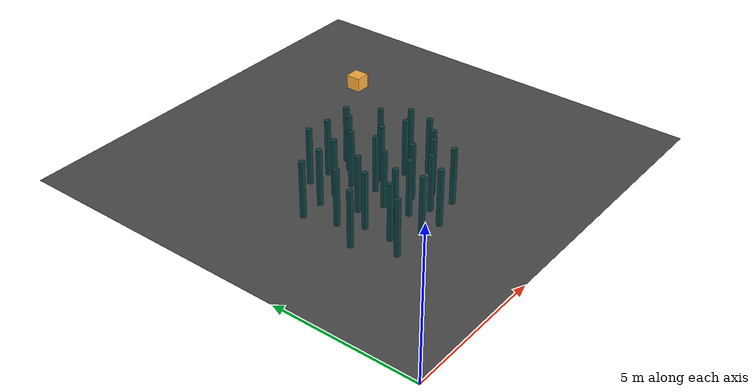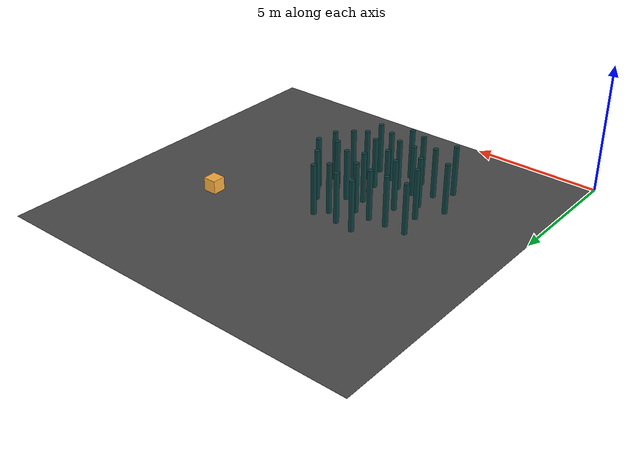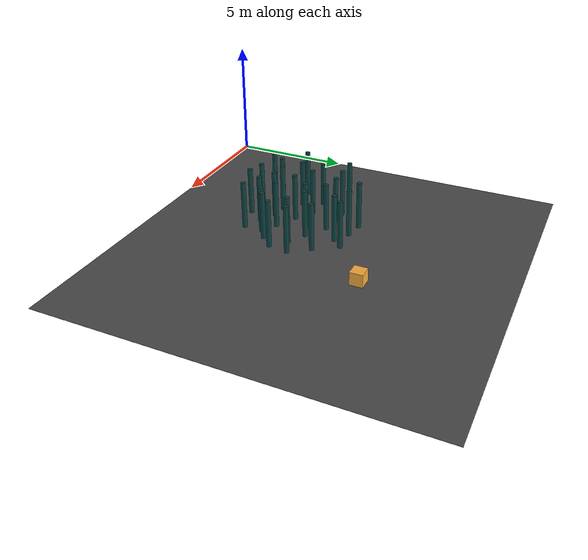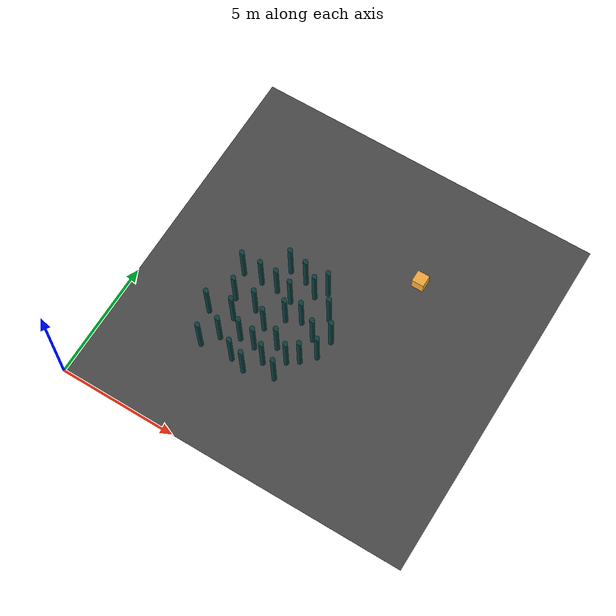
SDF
<sdf version="1.6">
 <world name="default">
  <light name="sun" type="directional">
   <pose>0 0 10 0 -0 0</pose>
   <diffuse>0.8 0.8 0.8 1</diffuse>
   <specular>0.2 0.2 0.2 1</specular>
   <attenuation>
    <range>1000</range>
    <constant>0.9</constant>
    <linear>0.01</linear>
    <quadratic>0.001</quadratic>
   </attenuation>
   <direction>-0.5 0.1 -0.9</direction>
  </light>
  <plugin name="ros_interface_plugin" filename="librotors_gazebo_ros_interface_plugin.so"/>
  <gravity>0 0 -9.8</gravity>
  <magnetic_field>6e-06 2.3e-05 -4.2e-05</magnetic_field>
  <atmosphere type="adiabatic"/>
  <physics name="default_physics" default="0" type="ode">
   <max_step_size>0.001</max_step_size>
   <real_time_factor>1</real_time_factor>
   <real_time_update_rate>1000</real_time_update_rate>
  </physics>
  <scene><ambient>0.95 0.95 0.95 1</ambient><background>1 1 1 1</background><shadows>1</shadows></scene>
  <spherical_coordinates>
   <surface_model>EARTH_WGS84</surface_model>
   <latitude_deg>0</latitude_deg>
   <longitude_deg>0</longitude_deg>
   <elevation>0</elevation>
   <heading_deg>0</heading_deg>
  </spherical_coordinates>
  <model name="env_plane">
   <link name="link">
    <inertial>
     <mass>1</mass>
     <inertia><ixx>1</ixx><ixy>0</ixy><ixz>0</ixz><iyy>1</iyy><iyz>0</iyz><izz>1</izz></inertia>
    </inertial>
    <visual name="visual">
     <cast_shadows>0</cast_shadows>
     <geometry><box><size>15 15 0.01</size></box></geometry>
     <material>
      <script>
       <uri>model://asphalt_plane/materials/scripts</uri>
       <uri>model://asphalt_plane/materials/textures</uri>
       <name>vrc/asphalt</name>
      </script>
      <shader type="pixel"><normal_map>__default__</normal_map></shader>
      <diffuse>0.7 0.7 0.7 1</diffuse>
      <ambient>0.5 0.5 0.5 1</ambient>
      <specular>0.5 0.5 0.5 1</specular>
      <emissive>0.7 0.7 0.7 1</emissive>
     </material>
    </visual>
    <collision name="collision">
     <geometry><box><size>20 20 0.1</size></box></geometry>
     <surface>
      <friction>
       <ode><mu>1</mu><mu2>1</mu2><fdir1>0 0 0</fdir1><slip1>0</slip1><slip2>0</slip2></ode>
       <torsional>
        <coefficient>1</coefficient>
        <patch_radius>0</patch_radius>
        <surface_radius>0</surface_radius>
        <use_patch_radius>1</use_patch_radius>
        <ode><slip>0</slip></ode>
       </torsional>
      </friction>
      <bounce><restitution_coefficient>0</restitution_coefficient><threshold>1e+06</threshold></bounce>
      <contact>
       <collide_without_contact>0</collide_without_contact>
       <collide_without_contact_bitmask>1</collide_without_contact_bitmask>
       <collide_bitmask>1</collide_bitmask>
       <ode>
        <soft_cfm>0</soft_cfm>
        <soft_erp>0.2</soft_erp>
        <kp>1e+13</kp>
        <kd>1</kd>
        <max_vel>0.01</max_vel>
        <min_depth>0</min_depth>
       </ode>
       <bullet>
        <split_impulse>1</split_impulse>
        <split_impulse_penetration_threshold>-0.01</split_impulse_penetration_threshold>
        <soft_cfm>0</soft_cfm>
        <soft_erp>0.2</soft_erp>
        <kp>1e+13</kp>
        <kd>1</kd>
       </bullet>
      </contact>
     </surface>
    </collision>
   </link>
   <static>1</static>
   <pose>7.5 7.5 0 0 -0 0</pose>
  </model>
  <model name="obstacle">
   <link name="link">
    <inertial>
     <mass>112.569</mass>
     <inertia><ixx>33.2512</ixx><ixy>0</ixy><ixz>0</ixz><iyy>33.2512</iyy><iyz>0</iyz><izz>0.537779</izz></inertia>
    </inertial>
    <visual name="visual">
     <geometry><cylinder><radius>0.1</radius><length>2</length></cylinder></geometry>
     <material>
      <script><name>Gazebo/Grey</name><uri>file://media/materials/scripts/gazebo.material</uri></script>
      <shader type="pixel"><normal_map>__default__</normal_map></shader>
      <ambient>0.05 0.25 0.25 1</ambient>
      <diffuse>0.3 0.3 0.3 1</diffuse>
      <specular>0.01 0.01 0.01 1</specular>
      <emissive>0.1 0.1 0.1 1</emissive>
      <lighting>1</lighting>
     </material>
    </visual>
    <collision name="collision">
     <geometry><cylinder><radius>0.097748</radius><length>1.87509</length></cylinder></geometry>
     <surface>
      <friction>
       <ode><mu>1</mu><mu2>1</mu2><fdir1>0 0 0</fdir1><slip1>0</slip1><slip2>0</slip2></ode>
       <torsional>
        <coefficient>1</coefficient>
        <patch_radius>0</patch_radius>
        <surface_radius>0</surface_radius>
        <use_patch_radius>1</use_patch_radius>
        <ode><slip>0</slip></ode>
       </torsional>
      </friction>
      <bounce><restitution_coefficient>0</restitution_coefficient><threshold>1e+06</threshold></bounce>
      <contact>
       <collide_without_contact>0</collide_without_contact>
       <collide_without_contact_bitmask>1</collide_without_contact_bitmask>
       <collide_bitmask>1</collide_bitmask>
       <ode>
        <soft_cfm>0</soft_cfm>
        <soft_erp>0.2</soft_erp>
        <kp>1e+13</kp>
        <kd>1</kd>
        <max_vel>0.01</max_vel>
        <min_depth>0</min_depth>
       </ode>
       <bullet>
        <split_impulse>1</split_impulse>
        <split_impulse_penetration_threshold>-0.01</split_impulse_penetration_threshold>
        <soft_cfm>0</soft_cfm>
        <soft_erp>0.2</soft_erp>
        <kp>1e+13</kp>
        <kd>1</kd>
       </bullet>
      </contact>
     </surface>
    </collision>
   </link>
   <static>0</static>
   <pose>8.04155 5.51694 0.987541 -5.2e-05 2.2e-05 0.010854</pose>
  </model>
  <model name="obstacle_clone_0">
   <link name="link">
    <inertial>
     <mass>112.569</mass>
     <inertia><ixx>33.2512</ixx><ixy>0</ixy><ixz>0</ixz><iyy>33.2512</iyy><iyz>0</iyz><izz>0.537779</izz></inertia>
    </inertial>
    <visual name="visual">
     <geometry><cylinder><radius>0.1</radius><length>2</length></cylinder></geometry>
     <material>
      <script><name>Gazebo/Grey</name><uri>file://media/materials/scripts/gazebo.material</uri></script>
      <shader type="pixel"><normal_map>__default__</normal_map></shader>
      <ambient>0.05 0.25 0.25 1</ambient>
      <diffuse>0.3 0.3 0.3 1</diffuse>
      <specular>0.01 0.01 0.01 1</specular>
      <emissive>0.1 0.1 0.1 1</emissive>
      <lighting>1</lighting>
     </material>
    </visual>
    <collision name="collision">
     <geometry><cylinder><radius>0.097748</radius><length>1.87509</length></cylinder></geometry>
     <surface>
      <friction>
       <ode><mu>1</mu><mu2>1</mu2><fdir1>0 0 0</fdir1><slip1>0</slip1><slip2>0</slip2></ode>
       <torsional>
        <coefficient>1</coefficient>
        <patch_radius>0</patch_radius>
        <surface_radius>0</surface_radius>
        <use_patch_radius>1</use_patch_radius>
        <ode><slip>0</slip></ode>
       </torsional>
      </friction>
      <bounce><restitution_coefficient>0</restitution_coefficient><threshold>1e+06</threshold></bounce>
      <contact>
       <collide_without_contact>0</collide_without_contact>
       <collide_without_contact_bitmask>1</collide_without_contact_bitmask>
       <collide_bitmask>1</collide_bitmask>
       <ode>
        <soft_cfm>0</soft_cfm>
        <soft_erp>0.2</soft_erp>
        <kp>1e+13</kp>
        <kd>1</kd>
        <max_vel>0.01</max_vel>
        <min_depth>0</min_depth>
       </ode>
       <bullet>
        <split_impulse>1</split_impulse>
        <split_impulse_penetration_threshold>-0.01</split_impulse_penetration_threshold>
        <soft_cfm>0</soft_cfm>
        <soft_erp>0.2</soft_erp>
        <kp>1e+13</kp>
        <kd>1</kd>
       </bullet>
      </contact>
     </surface>
    </collision>
   </link>
   <static>0</static>
   <pose>3.40506 5.00264 0.987551 -5.6e-05 2.7e-05 0.015402</pose>
  </model>
  <model name="obstacle_clone_1">
   <link name="link">
    <inertial>
     <mass>112.569</mass>
     <inertia><ixx>33.2512</ixx><ixy>0</ixy><ixz>0</ixz><iyy>33.2512</iyy><iyz>0</iyz><izz>0.537779</izz></inertia>
    </inertial>
    <visual name="visual">
     <geometry><cylinder><radius>0.1</radius><length>2</length></cylinder></geometry>
     <material>
      <script><name>Gazebo/Grey</name><uri>file://media/materials/scripts/gazebo.material</uri></script>
      <shader type="pixel"><normal_map>__default__</normal_map></shader>
      <ambient>0.05 0.25 0.25 1</ambient>
      <diffuse>0.3 0.3 0.3 1</diffuse>
      <specular>0.01 0.01 0.01 1</specular>
      <emissive>0.1 0.1 0.1 1</emissive>
      <lighting>1</lighting>
     </material>
    </visual>
    <collision name="collision">
     <geometry><cylinder><radius>0.097748</radius><length>1.87509</length></cylinder></geometry>
     <surface>
      <friction>
       <ode><mu>1</mu><mu2>1</mu2><fdir1>0 0 0</fdir1><slip1>0</slip1><slip2>0</slip2></ode>
       <torsional>
        <coefficient>1</coefficient>
        <patch_radius>0</patch_radius>
        <surface_radius>0</surface_radius>
        <use_patch_radius>1</use_patch_radius>
        <ode><slip>0</slip></ode>
       </torsional>
      </friction>
      <bounce><restitution_coefficient>0</restitution_coefficient><threshold>1e+06</threshold></bounce>
      <contact>
       <collide_without_contact>0</collide_without_contact>
       <collide_without_contact_bitmask>1</collide_without_contact_bitmask>
       <collide_bitmask>1</collide_bitmask>
       <ode>
        <soft_cfm>0</soft_cfm>
        <soft_erp>0.2</soft_erp>
        <kp>1e+13</kp>
        <kd>1</kd>
        <max_vel>0.01</max_vel>
        <min_depth>0</min_depth>
       </ode>
       <bullet>
        <split_impulse>1</split_impulse>
        <split_impulse_penetration_threshold>-0.01</split_impulse_penetration_threshold>
        <soft_cfm>0</soft_cfm>
        <soft_erp>0.2</soft_erp>
        <kp>1e+13</kp>
        <kd>1</kd>
       </bullet>
      </contact>
     </surface>
    </collision>
   </link>
   <static>0</static>
   <pose>5.64544 5.48256 0.987542 -6e-05 2.6e-05 0.015098</pose>
  </model>
  <model name="obstacle_clone_2">
   <link name="link">
    <inertial>
     <mass>112.569</mass>
     <inertia><ixx>33.2512</ixx><ixy>0</ixy><ixz>0</ixz><iyy>33.2512</iyy><iyz>0</iyz><izz>0.537779</izz></inertia>
    </inertial>
    <visual name="visual">
     <geometry><cylinder><radius>0.1</radius><length>2</length></cylinder></geometry>
     <material>
      <script><name>Gazebo/Grey</name><uri>file://media/materials/scripts/gazebo.material</uri></script>
      <shader type="pixel"><normal_map>__default__</normal_map></shader>
      <ambient>0.05 0.25 0.25 1</ambient>
      <diffuse>0.3 0.3 0.3 1</diffuse>
      <specular>0.01 0.01 0.01 1</specular>
      <emissive>0.1 0.1 0.1 1</emissive>
      <lighting>1</lighting>
     </material>
    </visual>
    <collision name="collision">
     <geometry><cylinder><radius>0.097748</radius><length>1.87509</length></cylinder></geometry>
     <surface>
      <friction>
       <ode><mu>1</mu><mu2>1</mu2><fdir1>0 0 0</fdir1><slip1>0</slip1><slip2>0</slip2></ode>
       <torsional>
        <coefficient>1</coefficient>
        <patch_radius>0</patch_radius>
        <surface_radius>0</surface_radius>
        <use_patch_radius>1</use_patch_radius>
        <ode><slip>0</slip></ode>
       </torsional>
      </friction>
      <bounce><restitution_coefficient>0</restitution_coefficient><threshold>1e+06</threshold></bounce>
      <contact>
       <collide_without_contact>0</collide_without_contact>
       <collide_without_contact_bitmask>1</collide_without_contact_bitmask>
       <collide_bitmask>1</collide_bitmask>
       <ode>
        <soft_cfm>0</soft_cfm>
        <soft_erp>0.2</soft_erp>
        <kp>1e+13</kp>
        <kd>1</kd>
        <max_vel>0.01</max_vel>
        <min_depth>0</min_depth>
       </ode>
       <bullet>
        <split_impulse>1</split_impulse>
        <split_impulse_penetration_threshold>-0.01</split_impulse_penetration_threshold>
        <soft_cfm>0</soft_cfm>
        <soft_erp>0.2</soft_erp>
        <kp>1e+13</kp>
        <kd>1</kd>
       </bullet>
      </contact>
     </surface>
    </collision>
   </link>
   <static>0</static>
   <pose>7.50227 6.05734 0.987542 -6e-05 2.8e-05 0.008708</pose>
  </model>
  <model name="obstacle_clone_3">
   <link name="link">
    <inertial>
     <mass>112.569</mass>
     <inertia><ixx>33.2512</ixx><ixy>0</ixy><ixz>0</ixz><iyy>33.2512</iyy><iyz>0</iyz><izz>0.537779</izz></inertia>
    </inertial>
    <visual name="visual">
     <geometry><cylinder><radius>0.1</radius><length>2</length></cylinder></geometry>
     <material>
      <script><name>Gazebo/Grey</name><uri>file://media/materials/scripts/gazebo.material</uri></script>
      <shader type="pixel"><normal_map>__default__</normal_map></shader>
      <ambient>0.05 0.25 0.25 1</ambient>
      <diffuse>0.3 0.3 0.3 1</diffuse>
      <specular>0.01 0.01 0.01 1</specular>
      <emissive>0.1 0.1 0.1 1</emissive>
      <lighting>1</lighting>
     </material>
    </visual>
    <collision name="collision">
     <geometry><cylinder><radius>0.097748</radius><length>1.87509</length></cylinder></geometry>
     <surface>
      <friction>
       <ode><mu>1</mu><mu2>1</mu2><fdir1>0 0 0</fdir1><slip1>0</slip1><slip2>0</slip2></ode>
       <torsional>
        <coefficient>1</coefficient>
        <patch_radius>0</patch_radius>
        <surface_radius>0</surface_radius>
        <use_patch_radius>1</use_patch_radius>
        <ode><slip>0</slip></ode>
       </torsional>
      </friction>
      <bounce><restitution_coefficient>0</restitution_coefficient><threshold>1e+06</threshold></bounce>
      <contact>
       <collide_without_contact>0</collide_without_contact>
       <collide_without_contact_bitmask>1</collide_without_contact_bitmask>
       <collide_bitmask>1</collide_bitmask>
       <ode>
        <soft_cfm>0</soft_cfm>
        <soft_erp>0.2</soft_erp>
        <kp>1e+13</kp>
        <kd>1</kd>
        <max_vel>0.01</max_vel>
        <min_depth>0</min_depth>
       </ode>
       <bullet>
        <split_impulse>1</split_impulse>
        <split_impulse_penetration_threshold>-0.01</split_impulse_penetration_threshold>
        <soft_cfm>0</soft_cfm>
        <soft_erp>0.2</soft_erp>
        <kp>1e+13</kp>
        <kd>1</kd>
       </bullet>
      </contact>
     </surface>
    </collision>
   </link>
   <static>0</static>
   <pose>4.51879 7.09694 0.987544 -3.2e-05 1.5e-05 0.004475</pose>
  </model>
  <model name="obstacle_clone_4">
   <link name="link">
    <inertial>
     <mass>112.569</mass>
     <inertia><ixx>33.2512</ixx><ixy>0</ixy><ixz>0</ixz><iyy>33.2512</iyy><iyz>0</iyz><izz>0.537779</izz></inertia>
    </inertial>
    <visual name="visual">
     <geometry><cylinder><radius>0.1</radius><length>2</length></cylinder></geometry>
     <material>
      <script><name>Gazebo/Grey</name><uri>file://media/materials/scripts/gazebo.material</uri></script>
      <shader type="pixel"><normal_map>__default__</normal_map></shader>
      <ambient>0.05 0.25 0.25 1</ambient>
      <diffuse>0.3 0.3 0.3 1</diffuse>
      <specular>0.01 0.01 0.01 1</specular>
      <emissive>0.1 0.1 0.1 1</emissive>
      <lighting>1</lighting>
     </material>
    </visual>
    <collision name="collision">
     <geometry><cylinder><radius>0.097748</radius><length>1.87509</length></cylinder></geometry>
     <surface>
      <friction>
       <ode><mu>1</mu><mu2>1</mu2><fdir1>0 0 0</fdir1><slip1>0</slip1><slip2>0</slip2></ode>
       <torsional>
        <coefficient>1</coefficient>
        <patch_radius>0</patch_radius>
        <surface_radius>0</surface_radius>
        <use_patch_radius>1</use_patch_radius>
        <ode><slip>0</slip></ode>
       </torsional>
      </friction>
      <bounce><restitution_coefficient>0</restitution_coefficient><threshold>1e+06</threshold></bounce>
      <contact>
       <collide_without_contact>0</collide_without_contact>
       <collide_without_contact_bitmask>1</collide_without_contact_bitmask>
       <collide_bitmask>1</collide_bitmask>
       <ode>
        <soft_cfm>0</soft_cfm>
        <soft_erp>0.2</soft_erp>
        <kp>1e+13</kp>
        <kd>1</kd>
        <max_vel>0.01</max_vel>
        <min_depth>0</min_depth>
       </ode>
       <bullet>
        <split_impulse>1</split_impulse>
        <split_impulse_penetration_threshold>-0.01</split_impulse_penetration_threshold>
        <soft_cfm>0</soft_cfm>
        <soft_erp>0.2</soft_erp>
        <kp>1e+13</kp>
        <kd>1</kd>
       </bullet>
      </contact>
     </surface>
    </collision>
   </link>
   <static>0</static>
   <pose>4.3863 4.28366 0.987541 -5e-05 2.3e-05 0.013957</pose>
  </model>
  <model name="obstacle_clone_5">
   <link name="link">
    <inertial>
     <mass>112.569</mass>
     <inertia><ixx>33.2512</ixx><ixy>0</ixy><ixz>0</ixz><iyy>33.2512</iyy><iyz>0</iyz><izz>0.537779</izz></inertia>
    </inertial>
    <visual name="visual">
     <geometry><cylinder><radius>0.1</radius><length>2</length></cylinder></geometry>
     <material>
      <script><name>Gazebo/Grey</name><uri>file://media/materials/scripts/gazebo.material</uri></script>
      <shader type="pixel"><normal_map>__default__</normal_map></shader>
      <ambient>0.05 0.25 0.25 1</ambient>
      <diffuse>0.3 0.3 0.3 1</diffuse>
      <specular>0.01 0.01 0.01 1</specular>
      <emissive>0.1 0.1 0.1 1</emissive>
      <lighting>1</lighting>
     </material>
    </visual>
    <collision name="collision">
     <geometry><cylinder><radius>0.097748</radius><length>1.87509</length></cylinder></geometry>
     <surface>
      <friction>
       <ode><mu>1</mu><mu2>1</mu2><fdir1>0 0 0</fdir1><slip1>0</slip1><slip2>0</slip2></ode>
       <torsional>
        <coefficient>1</coefficient>
        <patch_radius>0</patch_radius>
        <surface_radius>0</surface_radius>
        <use_patch_radius>1</use_patch_radius>
        <ode><slip>0</slip></ode>
       </torsional>
      </friction>
      <bounce><restitution_coefficient>0</restitution_coefficient><threshold>1e+06</threshold></bounce>
      <contact>
       <collide_without_contact>0</collide_without_contact>
       <collide_without_contact_bitmask>1</collide_without_contact_bitmask>
       <collide_bitmask>1</collide_bitmask>
       <ode>
        <soft_cfm>0</soft_cfm>
        <soft_erp>0.2</soft_erp>
        <kp>1e+13</kp>
        <kd>1</kd>
        <max_vel>0.01</max_vel>
        <min_depth>0</min_depth>
       </ode>
       <bullet>
        <split_impulse>1</split_impulse>
        <split_impulse_penetration_threshold>-0.01</split_impulse_penetration_threshold>
        <soft_cfm>0</soft_cfm>
        <soft_erp>0.2</soft_erp>
        <kp>1e+13</kp>
        <kd>1</kd>
       </bullet>
      </contact>
     </surface>
    </collision>
   </link>
   <static>0</static>
   <pose>4.00006 5.99998 0.987543 -2.8e-05 1.4e-05 0.0121</pose>
  </model>
  <model name="obstacle_clone_6">
   <link name="link">
    <inertial>
     <mass>112.569</mass>
     <inertia><ixx>33.2512</ixx><ixy>0</ixy><ixz>0</ixz><iyy>33.2512</iyy><iyz>0</iyz><izz>0.537779</izz></inertia>
    </inertial>
    <visual name="visual">
     <geometry><cylinder><radius>0.1</radius><length>2</length></cylinder></geometry>
     <material>
      <script><name>Gazebo/Grey</name><uri>file://media/materials/scripts/gazebo.material</uri></script>
      <shader type="pixel"><normal_map>__default__</normal_map></shader>
      <ambient>0.05 0.25 0.25 1</ambient>
      <diffuse>0.3 0.3 0.3 1</diffuse>
      <specular>0.01 0.01 0.01 1</specular>
      <emissive>0.1 0.1 0.1 1</emissive>
      <lighting>1</lighting>
     </material>
    </visual>
    <collision name="collision">
     <geometry><cylinder><radius>0.097748</radius><length>1.87509</length></cylinder></geometry>
     <surface>
      <friction>
       <ode><mu>1</mu><mu2>1</mu2><fdir1>0 0 0</fdir1><slip1>0</slip1><slip2>0</slip2></ode>
       <torsional>
        <coefficient>1</coefficient>
        <patch_radius>0</patch_radius>
        <surface_radius>0</surface_radius>
        <use_patch_radius>1</use_patch_radius>
        <ode><slip>0</slip></ode>
       </torsional>
      </friction>
      <bounce><restitution_coefficient>0</restitution_coefficient><threshold>1e+06</threshold></bounce>
      <contact>
       <collide_without_contact>0</collide_without_contact>
       <collide_without_contact_bitmask>1</collide_without_contact_bitmask>
       <collide_bitmask>1</collide_bitmask>
       <ode>
        <soft_cfm>0</soft_cfm>
        <soft_erp>0.2</soft_erp>
        <kp>1e+13</kp>
        <kd>1</kd>
        <max_vel>0.01</max_vel>
        <min_depth>0</min_depth>
       </ode>
       <bullet>
        <split_impulse>1</split_impulse>
        <split_impulse_penetration_threshold>-0.01</split_impulse_penetration_threshold>
        <soft_cfm>0</soft_cfm>
        <soft_erp>0.2</soft_erp>
        <kp>1e+13</kp>
        <kd>1</kd>
       </bullet>
      </contact>
     </surface>
    </collision>
   </link>
   <static>0</static>
   <pose>6.51285 5.05444 0.98755 -5.2e-05 2.5e-05 0.015599</pose>
  </model>
  <model name="obstacle_clone_7">
   <link name="link">
    <inertial>
     <mass>112.569</mass>
     <inertia><ixx>33.2512</ixx><ixy>0</ixy><ixz>0</ixz><iyy>33.2512</iyy><iyz>0</iyz><izz>0.537779</izz></inertia>
    </inertial>
    <visual name="visual">
     <geometry><cylinder><radius>0.1</radius><length>2</length></cylinder></geometry>
     <material>
      <script><name>Gazebo/Grey</name><uri>file://media/materials/scripts/gazebo.material</uri></script>
      <shader type="pixel"><normal_map>__default__</normal_map></shader>
      <ambient>0.05 0.25 0.25 1</ambient>
      <diffuse>0.3 0.3 0.3 1</diffuse>
      <specular>0.01 0.01 0.01 1</specular>
      <emissive>0.1 0.1 0.1 1</emissive>
      <lighting>1</lighting>
     </material>
    </visual>
    <collision name="collision">
     <geometry><cylinder><radius>0.097748</radius><length>1.87509</length></cylinder></geometry>
     <surface>
      <friction>
       <ode><mu>1</mu><mu2>1</mu2><fdir1>0 0 0</fdir1><slip1>0</slip1><slip2>0</slip2></ode>
       <torsional>
        <coefficient>1</coefficient>
        <patch_radius>0</patch_radius>
        <surface_radius>0</surface_radius>
        <use_patch_radius>1</use_patch_radius>
        <ode><slip>0</slip></ode>
       </torsional>
      </friction>
      <bounce><restitution_coefficient>0</restitution_coefficient><threshold>1e+06</threshold></bounce>
      <contact>
       <collide_without_contact>0</collide_without_contact>
       <collide_without_contact_bitmask>1</collide_without_contact_bitmask>
       <collide_bitmask>1</collide_bitmask>
       <ode>
        <soft_cfm>0</soft_cfm>
        <soft_erp>0.2</soft_erp>
        <kp>1e+13</kp>
        <kd>1</kd>
        <max_vel>0.01</max_vel>
        <min_depth>0</min_depth>
       </ode>
       <bullet>
        <split_impulse>1</split_impulse>
        <split_impulse_penetration_threshold>-0.01</split_impulse_penetration_threshold>
        <soft_cfm>0</soft_cfm>
        <soft_erp>0.2</soft_erp>
        <kp>1e+13</kp>
        <kd>1</kd>
       </bullet>
      </contact>
     </surface>
    </collision>
   </link>
   <static>0</static>
   <pose>5.25653 3.76481 0.987542 -6.1e-05 2.9e-05 0.02062</pose>
  </model>
  <model name="obstacle_clone_8">
   <link name="link">
    <inertial>
     <mass>112.569</mass>
     <inertia><ixx>33.2512</ixx><ixy>0</ixy><ixz>0</ixz><iyy>33.2512</iyy><iyz>0</iyz><izz>0.537779</izz></inertia>
    </inertial>
    <visual name="visual">
     <geometry><cylinder><radius>0.1</radius><length>2</length></cylinder></geometry>
     <material>
      <script><name>Gazebo/Grey</name><uri>file://media/materials/scripts/gazebo.material</uri></script>
      <shader type="pixel"><normal_map>__default__</normal_map></shader>
      <ambient>0.05 0.25 0.25 1</ambient>
      <diffuse>0.3 0.3 0.3 1</diffuse>
      <specular>0.01 0.01 0.01 1</specular>
      <emissive>0.1 0.1 0.1 1</emissive>
      <lighting>1</lighting>
     </material>
    </visual>
    <collision name="collision">
     <geometry><cylinder><radius>0.097748</radius><length>1.87509</length></cylinder></geometry>
     <surface>
      <friction>
       <ode><mu>1</mu><mu2>1</mu2><fdir1>0 0 0</fdir1><slip1>0</slip1><slip2>0</slip2></ode>
       <torsional>
        <coefficient>1</coefficient>
        <patch_radius>0</patch_radius>
        <surface_radius>0</surface_radius>
        <use_patch_radius>1</use_patch_radius>
        <ode><slip>0</slip></ode>
       </torsional>
      </friction>
      <bounce><restitution_coefficient>0</restitution_coefficient><threshold>1e+06</threshold></bounce>
      <contact>
       <collide_without_contact>0</collide_without_contact>
       <collide_without_contact_bitmask>1</collide_without_contact_bitmask>
       <collide_bitmask>1</collide_bitmask>
       <ode>
        <soft_cfm>0</soft_cfm>
        <soft_erp>0.2</soft_erp>
        <kp>1e+13</kp>
        <kd>1</kd>
        <max_vel>0.01</max_vel>
        <min_depth>0</min_depth>
       </ode>
       <bullet>
        <split_impulse>1</split_impulse>
        <split_impulse_penetration_threshold>-0.01</split_impulse_penetration_threshold>
        <soft_cfm>0</soft_cfm>
        <soft_erp>0.2</soft_erp>
        <kp>1e+13</kp>
        <kd>1</kd>
       </bullet>
      </contact>
     </surface>
    </collision>
   </link>
   <static>0</static>
   <pose>4.96005 5.95574 0.987552 -6.2e-05 2.9e-05 0.015441</pose>
  </model>
  <model name="obstacle_clone_9">
   <link name="link">
    <inertial>
     <mass>112.569</mass>
     <inertia><ixx>33.2512</ixx><ixy>0</ixy><ixz>0</ixz><iyy>33.2512</iyy><iyz>0</iyz><izz>0.537779</izz></inertia>
    </inertial>
    <visual name="visual">
     <geometry><cylinder><radius>0.1</radius><length>2</length></cylinder></geometry>
     <material>
      <script><name>Gazebo/Grey</name><uri>file://media/materials/scripts/gazebo.material</uri></script>
      <shader type="pixel"><normal_map>__default__</normal_map></shader>
      <ambient>0.05 0.25 0.25 1</ambient>
      <diffuse>0.3 0.3 0.3 1</diffuse>
      <specular>0.01 0.01 0.01 1</specular>
      <emissive>0.1 0.1 0.1 1</emissive>
      <lighting>1</lighting>
     </material>
    </visual>
    <collision name="collision">
     <geometry><cylinder><radius>0.097748</radius><length>1.87509</length></cylinder></geometry>
     <surface>
      <friction>
       <ode><mu>1</mu><mu2>1</mu2><fdir1>0 0 0</fdir1><slip1>0</slip1><slip2>0</slip2></ode>
       <torsional>
        <coefficient>1</coefficient>
        <patch_radius>0</patch_radius>
        <surface_radius>0</surface_radius>
        <use_patch_radius>1</use_patch_radius>
        <ode><slip>0</slip></ode>
       </torsional>
      </friction>
      <bounce><restitution_coefficient>0</restitution_coefficient><threshold>1e+06</threshold></bounce>
      <contact>
       <collide_without_contact>0</collide_without_contact>
       <collide_without_contact_bitmask>1</collide_without_contact_bitmask>
       <collide_bitmask>1</collide_bitmask>
       <ode>
        <soft_cfm>0</soft_cfm>
        <soft_erp>0.2</soft_erp>
        <kp>1e+13</kp>
        <kd>1</kd>
        <max_vel>0.01</max_vel>
        <min_depth>0</min_depth>
       </ode>
       <bullet>
        <split_impulse>1</split_impulse>
        <split_impulse_penetration_threshold>-0.01</split_impulse_penetration_threshold>
        <soft_cfm>0</soft_cfm>
        <soft_erp>0.2</soft_erp>
        <kp>1e+13</kp>
        <kd>1</kd>
       </bullet>
      </contact>
     </surface>
    </collision>
   </link>
   <static>0</static>
   <pose>7.1421 4.71785 0.987552 -6.3e-05 2.8e-05 0.108669</pose>
  </model>
  <model name="obstacle_clone_10">
   <link name="link">
    <inertial>
     <mass>112.569</mass>
     <inertia><ixx>33.2512</ixx><ixy>0</ixy><ixz>0</ixz><iyy>33.2512</iyy><iyz>0</iyz><izz>0.537779</izz></inertia>
    </inertial>
    <visual name="visual">
     <geometry><cylinder><radius>0.1</radius><length>2</length></cylinder></geometry>
     <material>
      <script><name>Gazebo/Grey</name><uri>file://media/materials/scripts/gazebo.material</uri></script>
      <shader type="pixel"><normal_map>__default__</normal_map></shader>
      <ambient>0.05 0.25 0.25 1</ambient>
      <diffuse>0.3 0.3 0.3 1</diffuse>
      <specular>0.01 0.01 0.01 1</specular>
      <emissive>0.1 0.1 0.1 1</emissive>
      <lighting>1</lighting>
     </material>
    </visual>
    <collision name="collision">
     <geometry><cylinder><radius>0.097748</radius><length>1.87509</length></cylinder></geometry>
     <surface>
      <friction>
       <ode><mu>1</mu><mu2>1</mu2><fdir1>0 0 0</fdir1><slip1>0</slip1><slip2>0</slip2></ode>
       <torsional>
        <coefficient>1</coefficient>
        <patch_radius>0</patch_radius>
        <surface_radius>0</surface_radius>
        <use_patch_radius>1</use_patch_radius>
        <ode><slip>0</slip></ode>
       </torsional>
      </friction>
      <bounce><restitution_coefficient>0</restitution_coefficient><threshold>1e+06</threshold></bounce>
      <contact>
       <collide_without_contact>0</collide_without_contact>
       <collide_without_contact_bitmask>1</collide_without_contact_bitmask>
       <collide_bitmask>1</collide_bitmask>
       <ode>
        <soft_cfm>0</soft_cfm>
        <soft_erp>0.2</soft_erp>
        <kp>1e+13</kp>
        <kd>1</kd>
        <max_vel>0.01</max_vel>
        <min_depth>0</min_depth>
       </ode>
       <bullet>
        <split_impulse>1</split_impulse>
        <split_impulse_penetration_threshold>-0.01</split_impulse_penetration_threshold>
        <soft_cfm>0</soft_cfm>
        <soft_erp>0.2</soft_erp>
        <kp>1e+13</kp>
        <kd>1</kd>
       </bullet>
      </contact>
     </surface>
    </collision>
   </link>
   <static>0</static>
   <pose>3.89885 3.66066 0.987552 -6.2e-05 2.8e-05 0.012829</pose>
  </model>
  <model name="obstacle_clone_11">
   <link name="link">
    <inertial>
     <mass>112.569</mass>
     <inertia><ixx>33.2512</ixx><ixy>0</ixy><ixz>0</ixz><iyy>33.2512</iyy><iyz>0</iyz><izz>0.537779</izz></inertia>
    </inertial>
    <visual name="visual">
     <geometry><cylinder><radius>0.1</radius><length>2</length></cylinder></geometry>
     <material>
      <script><name>Gazebo/Grey</name><uri>file://media/materials/scripts/gazebo.material</uri></script>
      <shader type="pixel"><normal_map>__default__</normal_map></shader>
      <ambient>0.05 0.25 0.25 1</ambient>
      <diffuse>0.3 0.3 0.3 1</diffuse>
      <specular>0.01 0.01 0.01 1</specular>
      <emissive>0.1 0.1 0.1 1</emissive>
      <lighting>1</lighting>
     </material>
    </visual>
    <collision name="collision">
     <geometry><cylinder><radius>0.097748</radius><length>1.87509</length></cylinder></geometry>
     <surface>
      <friction>
       <ode><mu>1</mu><mu2>1</mu2><fdir1>0 0 0</fdir1><slip1>0</slip1><slip2>0</slip2></ode>
       <torsional>
        <coefficient>1</coefficient>
        <patch_radius>0</patch_radius>
        <surface_radius>0</surface_radius>
        <use_patch_radius>1</use_patch_radius>
        <ode><slip>0</slip></ode>
       </torsional>
      </friction>
      <bounce><restitution_coefficient>0</restitution_coefficient><threshold>1e+06</threshold></bounce>
      <contact>
       <collide_without_contact>0</collide_without_contact>
       <collide_without_contact_bitmask>1</collide_without_contact_bitmask>
       <collide_bitmask>1</collide_bitmask>
       <ode>
        <soft_cfm>0</soft_cfm>
        <soft_erp>0.2</soft_erp>
        <kp>1e+13</kp>
        <kd>1</kd>
        <max_vel>0.01</max_vel>
        <min_depth>0</min_depth>
       </ode>
       <bullet>
        <split_impulse>1</split_impulse>
        <split_impulse_penetration_threshold>-0.01</split_impulse_penetration_threshold>
        <soft_cfm>0</soft_cfm>
        <soft_erp>0.2</soft_erp>
        <kp>1e+13</kp>
        <kd>1</kd>
       </bullet>
      </contact>
     </surface>
    </collision>
   </link>
   <static>0</static>
   <pose>5.23748 8.11375 0.987544 -2.8e-05 1.3e-05 0.014505</pose>
  </model>
  <model name="obstacle_clone_13">
   <link name="link">
    <inertial>
     <mass>112.569</mass>
     <inertia><ixx>33.2512</ixx><ixy>0</ixy><ixz>0</ixz><iyy>33.2512</iyy><iyz>0</iyz><izz>0.537779</izz></inertia>
    </inertial>
    <visual name="visual">
     <geometry><cylinder><radius>0.1</radius><length>2</length></cylinder></geometry>
     <material>
      <script><name>Gazebo/Grey</name><uri>file://media/materials/scripts/gazebo.material</uri></script>
      <shader type="pixel"><normal_map>__default__</normal_map></shader>
      <ambient>0.05 0.25 0.25 1</ambient>
      <diffuse>0.3 0.3 0.3 1</diffuse>
      <specular>0.01 0.01 0.01 1</specular>
      <emissive>0.1 0.1 0.1 1</emissive>
      <lighting>1</lighting>
     </material>
    </visual>
    <collision name="collision">
     <geometry><cylinder><radius>0.097748</radius><length>1.87509</length></cylinder></geometry>
     <surface>
      <friction>
       <ode><mu>1</mu><mu2>1</mu2><fdir1>0 0 0</fdir1><slip1>0</slip1><slip2>0</slip2></ode>
       <torsional>
        <coefficient>1</coefficient>
        <patch_radius>0</patch_radius>
        <surface_radius>0</surface_radius>
        <use_patch_radius>1</use_patch_radius>
        <ode><slip>0</slip></ode>
       </torsional>
      </friction>
      <bounce><restitution_coefficient>0</restitution_coefficient><threshold>1e+06</threshold></bounce>
      <contact>
       <collide_without_contact>0</collide_without_contact>
       <collide_without_contact_bitmask>1</collide_without_contact_bitmask>
       <collide_bitmask>1</collide_bitmask>
       <ode>
        <soft_cfm>0</soft_cfm>
        <soft_erp>0.2</soft_erp>
        <kp>1e+13</kp>
        <kd>1</kd>
        <max_vel>0.01</max_vel>
        <min_depth>0</min_depth>
       </ode>
       <bullet>
        <split_impulse>1</split_impulse>
        <split_impulse_penetration_threshold>-0.01</split_impulse_penetration_threshold>
        <soft_cfm>0</soft_cfm>
        <soft_erp>0.2</soft_erp>
        <kp>1e+13</kp>
        <kd>1</kd>
       </bullet>
      </contact>
     </surface>
    </collision>
   </link>
   <static>0</static>
   <pose>3.70207 7.07835 0.987541 -5.7e-05 2.5e-05 0.007591</pose>
  </model>
  <model name="obstacle_clone_14">
   <link name="link">
    <inertial>
     <mass>112.569</mass>
     <inertia><ixx>33.2512</ixx><ixy>0</ixy><ixz>0</ixz><iyy>33.2512</iyy><iyz>0</iyz><izz>0.537779</izz></inertia>
    </inertial>
    <visual name="visual">
     <geometry><cylinder><radius>0.1</radius><length>2</length></cylinder></geometry>
     <material>
      <script><name>Gazebo/Grey</name><uri>file://media/materials/scripts/gazebo.material</uri></script>
      <shader type="pixel"><normal_map>__default__</normal_map></shader>
      <ambient>0.05 0.25 0.25 1</ambient>
      <diffuse>0.3 0.3 0.3 1</diffuse>
      <specular>0.01 0.01 0.01 1</specular>
      <emissive>0.1 0.1 0.1 1</emissive>
      <lighting>1</lighting>
     </material>
    </visual>
    <collision name="collision">
     <geometry><cylinder><radius>0.097748</radius><length>1.87509</length></cylinder></geometry>
     <surface>
      <friction>
       <ode><mu>1</mu><mu2>1</mu2><fdir1>0 0 0</fdir1><slip1>0</slip1><slip2>0</slip2></ode>
       <torsional>
        <coefficient>1</coefficient>
        <patch_radius>0</patch_radius>
        <surface_radius>0</surface_radius>
        <use_patch_radius>1</use_patch_radius>
        <ode><slip>0</slip></ode>
       </torsional>
      </friction>
      <bounce><restitution_coefficient>0</restitution_coefficient><threshold>1e+06</threshold></bounce>
      <contact>
       <collide_without_contact>0</collide_without_contact>
       <collide_without_contact_bitmask>1</collide_without_contact_bitmask>
       <collide_bitmask>1</collide_bitmask>
       <ode>
        <soft_cfm>0</soft_cfm>
        <soft_erp>0.2</soft_erp>
        <kp>1e+13</kp>
        <kd>1</kd>
        <max_vel>0.01</max_vel>
        <min_depth>0</min_depth>
       </ode>
       <bullet>
        <split_impulse>1</split_impulse>
        <split_impulse_penetration_threshold>-0.01</split_impulse_penetration_threshold>
        <soft_cfm>0</soft_cfm>
        <soft_erp>0.2</soft_erp>
        <kp>1e+13</kp>
        <kd>1</kd>
       </bullet>
      </contact>
     </surface>
    </collision>
   </link>
   <static>0</static>
   <pose>6.9948 8.04761 0.987544 -3e-05 1.4e-05 0.013899</pose>
  </model>
  <model name="obstacle_clone_16">
   <link name="link">
    <inertial>
     <mass>112.569</mass>
     <inertia><ixx>33.2512</ixx><ixy>0</ixy><ixz>0</ixz><iyy>33.2512</iyy><iyz>0</iyz><izz>0.537779</izz></inertia>
    </inertial>
    <visual name="visual">
     <geometry><cylinder><radius>0.1</radius><length>2</length></cylinder></geometry>
     <material>
      <script><name>Gazebo/Grey</name><uri>file://media/materials/scripts/gazebo.material</uri></script>
      <shader type="pixel"><normal_map>__default__</normal_map></shader>
      <ambient>0.05 0.25 0.25 1</ambient>
      <diffuse>0.3 0.3 0.3 1</diffuse>
      <specular>0.01 0.01 0.01 1</specular>
      <emissive>0.1 0.1 0.1 1</emissive>
      <lighting>1</lighting>
     </material>
    </visual>
    <collision name="collision">
     <geometry><cylinder><radius>0.097748</radius><length>1.87509</length></cylinder></geometry>
     <surface>
      <friction>
       <ode><mu>1</mu><mu2>1</mu2><fdir1>0 0 0</fdir1><slip1>0</slip1><slip2>0</slip2></ode>
       <torsional>
        <coefficient>1</coefficient>
        <patch_radius>0</patch_radius>
        <surface_radius>0</surface_radius>
        <use_patch_radius>1</use_patch_radius>
        <ode><slip>0</slip></ode>
       </torsional>
      </friction>
      <bounce><restitution_coefficient>0</restitution_coefficient><threshold>1e+06</threshold></bounce>
      <contact>
       <collide_without_contact>0</collide_without_contact>
       <collide_without_contact_bitmask>1</collide_without_contact_bitmask>
       <collide_bitmask>1</collide_bitmask>
       <ode>
        <soft_cfm>0</soft_cfm>
        <soft_erp>0.2</soft_erp>
        <kp>1e+13</kp>
        <kd>1</kd>
        <max_vel>0.01</max_vel>
        <min_depth>0</min_depth>
       </ode>
       <bullet>
        <split_impulse>1</split_impulse>
        <split_impulse_penetration_threshold>-0.01</split_impulse_penetration_threshold>
        <soft_cfm>0</soft_cfm>
        <soft_erp>0.2</soft_erp>
        <kp>1e+13</kp>
        <kd>1</kd>
       </bullet>
      </contact>
     </surface>
    </collision>
   </link>
   <static>0</static>
   <pose>5.22691 7.10258 0.987541 -5.2e-05 2.2e-05 0.013813</pose>
  </model>
  <model name="obstacle_clone_17">
   <link name="link">
    <inertial>
     <mass>112.569</mass>
     <inertia><ixx>33.2512</ixx><ixy>0</ixy><ixz>0</ixz><iyy>33.2512</iyy><iyz>0</iyz><izz>0.537779</izz></inertia>
    </inertial>
    <visual name="visual">
     <geometry><cylinder><radius>0.1</radius><length>2</length></cylinder></geometry>
     <material>
      <script><name>Gazebo/Grey</name><uri>file://media/materials/scripts/gazebo.material</uri></script>
      <shader type="pixel"><normal_map>__default__</normal_map></shader>
      <ambient>0.05 0.25 0.25 1</ambient>
      <diffuse>0.3 0.3 0.3 1</diffuse>
      <specular>0.01 0.01 0.01 1</specular>
      <emissive>0.1 0.1 0.1 1</emissive>
      <lighting>1</lighting>
     </material>
    </visual>
    <collision name="collision">
     <geometry><cylinder><radius>0.097748</radius><length>1.87509</length></cylinder></geometry>
     <surface>
      <friction>
       <ode><mu>1</mu><mu2>1</mu2><fdir1>0 0 0</fdir1><slip1>0</slip1><slip2>0</slip2></ode>
       <torsional>
        <coefficient>1</coefficient>
        <patch_radius>0</patch_radius>
        <surface_radius>0</surface_radius>
        <use_patch_radius>1</use_patch_radius>
        <ode><slip>0</slip></ode>
       </torsional>
      </friction>
      <bounce><restitution_coefficient>0</restitution_coefficient><threshold>1e+06</threshold></bounce>
      <contact>
       <collide_without_contact>0</collide_without_contact>
       <collide_without_contact_bitmask>1</collide_without_contact_bitmask>
       <collide_bitmask>1</collide_bitmask>
       <ode>
        <soft_cfm>0</soft_cfm>
        <soft_erp>0.2</soft_erp>
        <kp>1e+13</kp>
        <kd>1</kd>
        <max_vel>0.01</max_vel>
        <min_depth>0</min_depth>
       </ode>
       <bullet>
        <split_impulse>1</split_impulse>
        <split_impulse_penetration_threshold>-0.01</split_impulse_penetration_threshold>
        <soft_cfm>0</soft_cfm>
        <soft_erp>0.2</soft_erp>
        <kp>1e+13</kp>
        <kd>1</kd>
       </bullet>
      </contact>
     </surface>
    </collision>
   </link>
   <static>0</static>
   <pose>5.89848 3.57186 0.987542 -5.6e-05 2.7e-05 0.01236</pose>
  </model>
  <model name="obstacle_clone_18">
   <link name="link">
    <inertial>
     <mass>112.569</mass>
     <inertia><ixx>33.2512</ixx><ixy>0</ixy><ixz>0</ixz><iyy>33.2512</iyy><iyz>0</iyz><izz>0.537779</izz></inertia>
    </inertial>
    <visual name="visual">
     <geometry><cylinder><radius>0.1</radius><length>2</length></cylinder></geometry>
     <material>
      <script><name>Gazebo/Grey</name><uri>file://media/materials/scripts/gazebo.material</uri></script>
      <shader type="pixel"><normal_map>__default__</normal_map></shader>
      <ambient>0.05 0.25 0.25 1</ambient>
      <diffuse>0.3 0.3 0.3 1</diffuse>
      <specular>0.01 0.01 0.01 1</specular>
      <emissive>0.1 0.1 0.1 1</emissive>
      <lighting>1</lighting>
     </material>
    </visual>
    <collision name="collision">
     <geometry><cylinder><radius>0.097748</radius><length>1.87509</length></cylinder></geometry>
     <surface>
      <friction>
       <ode><mu>1</mu><mu2>1</mu2><fdir1>0 0 0</fdir1><slip1>0</slip1><slip2>0</slip2></ode>
       <torsional>
        <coefficient>1</coefficient>
        <patch_radius>0</patch_radius>
        <surface_radius>0</surface_radius>
        <use_patch_radius>1</use_patch_radius>
        <ode><slip>0</slip></ode>
       </torsional>
      </friction>
      <bounce><restitution_coefficient>0</restitution_coefficient><threshold>1e+06</threshold></bounce>
      <contact>
       <collide_without_contact>0</collide_without_contact>
       <collide_without_contact_bitmask>1</collide_without_contact_bitmask>
       <collide_bitmask>1</collide_bitmask>
       <ode>
        <soft_cfm>0</soft_cfm>
        <soft_erp>0.2</soft_erp>
        <kp>1e+13</kp>
        <kd>1</kd>
        <max_vel>0.01</max_vel>
        <min_depth>0</min_depth>
       </ode>
       <bullet>
        <split_impulse>1</split_impulse>
        <split_impulse_penetration_threshold>-0.01</split_impulse_penetration_threshold>
        <soft_cfm>0</soft_cfm>
        <soft_erp>0.2</soft_erp>
        <kp>1e+13</kp>
        <kd>1</kd>
       </bullet>
      </contact>
     </surface>
    </collision>
   </link>
   <static>0</static>
   <pose>6.37048 4.24202 0.987551 -5.4e-05 2.5e-05 0.015671</pose>
  </model>
  <model name="obstacle_clone_19">
   <link name="link">
    <inertial>
     <mass>112.569</mass>
     <inertia><ixx>33.2512</ixx><ixy>0</ixy><ixz>0</ixz><iyy>33.2512</iyy><iyz>0</iyz><izz>0.537779</izz></inertia>
    </inertial>
    <visual name="visual">
     <geometry><cylinder><radius>0.1</radius><length>2</length></cylinder></geometry>
     <material>
      <script><name>Gazebo/Grey</name><uri>file://media/materials/scripts/gazebo.material</uri></script>
      <shader type="pixel"><normal_map>__default__</normal_map></shader>
      <ambient>0.05 0.25 0.25 1</ambient>
      <diffuse>0.3 0.3 0.3 1</diffuse>
      <specular>0.01 0.01 0.01 1</specular>
      <emissive>0.1 0.1 0.1 1</emissive>
      <lighting>1</lighting>
     </material>
    </visual>
    <collision name="collision">
     <geometry><cylinder><radius>0.097748</radius><length>1.87509</length></cylinder></geometry>
     <surface>
      <friction>
       <ode><mu>1</mu><mu2>1</mu2><fdir1>0 0 0</fdir1><slip1>0</slip1><slip2>0</slip2></ode>
       <torsional>
        <coefficient>1</coefficient>
        <patch_radius>0</patch_radius>
        <surface_radius>0</surface_radius>
        <use_patch_radius>1</use_patch_radius>
        <ode><slip>0</slip></ode>
       </torsional>
      </friction>
      <bounce><restitution_coefficient>0</restitution_coefficient><threshold>1e+06</threshold></bounce>
      <contact>
       <collide_without_contact>0</collide_without_contact>
       <collide_without_contact_bitmask>1</collide_without_contact_bitmask>
       <collide_bitmask>1</collide_bitmask>
       <ode>
        <soft_cfm>0</soft_cfm>
        <soft_erp>0.2</soft_erp>
        <kp>1e+13</kp>
        <kd>1</kd>
        <max_vel>0.01</max_vel>
        <min_depth>0</min_depth>
       </ode>
       <bullet>
        <split_impulse>1</split_impulse>
        <split_impulse_penetration_threshold>-0.01</split_impulse_penetration_threshold>
        <soft_cfm>0</soft_cfm>
        <soft_erp>0.2</soft_erp>
        <kp>1e+13</kp>
        <kd>1</kd>
       </bullet>
      </contact>
     </surface>
    </collision>
   </link>
   <static>0</static>
   <pose>5.9187 6.98158 0.987543 -3.1e-05 1.4e-05 0.005729</pose>
  </model>
  <model name="obstacle_clone_20">
   <link name="link">
    <inertial>
     <mass>112.569</mass>
     <inertia><ixx>33.2512</ixx><ixy>0</ixy><ixz>0</ixz><iyy>33.2512</iyy><iyz>0</iyz><izz>0.537779</izz></inertia>
    </inertial>
    <visual name="visual">
     <geometry><cylinder><radius>0.1</radius><length>2</length></cylinder></geometry>
     <material>
      <script><name>Gazebo/Grey</name><uri>file://media/materials/scripts/gazebo.material</uri></script>
      <shader type="pixel"><normal_map>__default__</normal_map></shader>
      <ambient>0.05 0.25 0.25 1</ambient>
      <diffuse>0.3 0.3 0.3 1</diffuse>
      <specular>0.01 0.01 0.01 1</specular>
      <emissive>0.1 0.1 0.1 1</emissive>
      <lighting>1</lighting>
     </material>
    </visual>
    <collision name="collision">
     <geometry><cylinder><radius>0.097748</radius><length>1.87509</length></cylinder></geometry>
     <surface>
      <friction>
       <ode><mu>1</mu><mu2>1</mu2><fdir1>0 0 0</fdir1><slip1>0</slip1><slip2>0</slip2></ode>
       <torsional>
        <coefficient>1</coefficient>
        <patch_radius>0</patch_radius>
        <surface_radius>0</surface_radius>
        <use_patch_radius>1</use_patch_radius>
        <ode><slip>0</slip></ode>
       </torsional>
      </friction>
      <bounce><restitution_coefficient>0</restitution_coefficient><threshold>1e+06</threshold></bounce>
      <contact>
       <collide_without_contact>0</collide_without_contact>
       <collide_without_contact_bitmask>1</collide_without_contact_bitmask>
       <collide_bitmask>1</collide_bitmask>
       <ode>
        <soft_cfm>0</soft_cfm>
        <soft_erp>0.2</soft_erp>
        <kp>1e+13</kp>
        <kd>1</kd>
        <max_vel>0.01</max_vel>
        <min_depth>0</min_depth>
       </ode>
       <bullet>
        <split_impulse>1</split_impulse>
        <split_impulse_penetration_threshold>-0.01</split_impulse_penetration_threshold>
        <soft_cfm>0</soft_cfm>
        <soft_erp>0.2</soft_erp>
        <kp>1e+13</kp>
        <kd>1</kd>
       </bullet>
      </contact>
     </surface>
    </collision>
   </link>
   <static>0</static>
   <pose>7.56138 5.01862 0.987543 -2.7e-05 1.3e-05 0.005645</pose>
  </model>
  <model name="obstacle_clone_21">
   <link name="link">
    <inertial>
     <mass>112.569</mass>
     <inertia><ixx>33.2512</ixx><ixy>0</ixy><ixz>0</ixz><iyy>33.2512</iyy><iyz>0</iyz><izz>0.537779</izz></inertia>
    </inertial>
    <visual name="visual">
     <geometry><cylinder><radius>0.1</radius><length>2</length></cylinder></geometry>
     <material>
      <script><name>Gazebo/Grey</name><uri>file://media/materials/scripts/gazebo.material</uri></script>
      <shader type="pixel"><normal_map>__default__</normal_map></shader>
      <ambient>0.05 0.25 0.25 1</ambient>
      <diffuse>0.3 0.3 0.3 1</diffuse>
      <specular>0.01 0.01 0.01 1</specular>
      <emissive>0.1 0.1 0.1 1</emissive>
      <lighting>1</lighting>
     </material>
    </visual>
    <collision name="collision">
     <geometry><cylinder><radius>0.097748</radius><length>1.87509</length></cylinder></geometry>
     <surface>
      <friction>
       <ode><mu>1</mu><mu2>1</mu2><fdir1>0 0 0</fdir1><slip1>0</slip1><slip2>0</slip2></ode>
       <torsional>
        <coefficient>1</coefficient>
        <patch_radius>0</patch_radius>
        <surface_radius>0</surface_radius>
        <use_patch_radius>1</use_patch_radius>
        <ode><slip>0</slip></ode>
       </torsional>
      </friction>
      <bounce><restitution_coefficient>0</restitution_coefficient><threshold>1e+06</threshold></bounce>
      <contact>
       <collide_without_contact>0</collide_without_contact>
       <collide_without_contact_bitmask>1</collide_without_contact_bitmask>
       <collide_bitmask>1</collide_bitmask>
       <ode>
        <soft_cfm>0</soft_cfm>
        <soft_erp>0.2</soft_erp>
        <kp>1e+13</kp>
        <kd>1</kd>
        <max_vel>0.01</max_vel>
        <min_depth>0</min_depth>
       </ode>
       <bullet>
        <split_impulse>1</split_impulse>
        <split_impulse_penetration_threshold>-0.01</split_impulse_penetration_threshold>
        <soft_cfm>0</soft_cfm>
        <soft_erp>0.2</soft_erp>
        <kp>1e+13</kp>
        <kd>1</kd>
       </bullet>
      </contact>
     </surface>
    </collision>
   </link>
   <static>0</static>
   <pose>6.00064 8.00009 0.987551 -6e-05 2.7e-05 0.015691</pose>
  </model>
  <model name="obstacle_clone_22">
   <link name="link">
    <inertial>
     <mass>112.569</mass>
     <inertia><ixx>33.2512</ixx><ixy>0</ixy><ixz>0</ixz><iyy>33.2512</iyy><iyz>0</iyz><izz>0.537779</izz></inertia>
    </inertial>
    <visual name="visual">
     <geometry><cylinder><radius>0.1</radius><length>2</length></cylinder></geometry>
     <material>
      <script><name>Gazebo/Grey</name><uri>file://media/materials/scripts/gazebo.material</uri></script>
      <shader type="pixel"><normal_map>__default__</normal_map></shader>
      <ambient>0.05 0.25 0.25 1</ambient>
      <diffuse>0.3 0.3 0.3 1</diffuse>
      <specular>0.01 0.01 0.01 1</specular>
      <emissive>0.1 0.1 0.1 1</emissive>
      <lighting>1</lighting>
     </material>
    </visual>
    <collision name="collision">
     <geometry><cylinder><radius>0.097748</radius><length>1.87509</length></cylinder></geometry>
     <surface>
      <friction>
       <ode><mu>1</mu><mu2>1</mu2><fdir1>0 0 0</fdir1><slip1>0</slip1><slip2>0</slip2></ode>
       <torsional>
        <coefficient>1</coefficient>
        <patch_radius>0</patch_radius>
        <surface_radius>0</surface_radius>
        <use_patch_radius>1</use_patch_radius>
        <ode><slip>0</slip></ode>
       </torsional>
      </friction>
      <bounce><restitution_coefficient>0</restitution_coefficient><threshold>1e+06</threshold></bounce>
      <contact>
       <collide_without_contact>0</collide_without_contact>
       <collide_without_contact_bitmask>1</collide_without_contact_bitmask>
       <collide_bitmask>1</collide_bitmask>
       <ode>
        <soft_cfm>0</soft_cfm>
        <soft_erp>0.2</soft_erp>
        <kp>1e+13</kp>
        <kd>1</kd>
        <max_vel>0.01</max_vel>
        <min_depth>0</min_depth>
       </ode>
       <bullet>
        <split_impulse>1</split_impulse>
        <split_impulse_penetration_threshold>-0.01</split_impulse_penetration_threshold>
        <soft_cfm>0</soft_cfm>
        <soft_erp>0.2</soft_erp>
        <kp>1e+13</kp>
        <kd>1</kd>
       </bullet>
      </contact>
     </surface>
    </collision>
   </link>
   <static>0</static>
   <pose>5.7506 4.60333 0.987542 -5.9e-05 2.4e-05 -0.089182</pose>
  </model>
  <model name="obstacle_clone_23">
   <link name="link">
    <inertial>
     <mass>112.569</mass>
     <inertia><ixx>33.2512</ixx><ixy>0</ixy><ixz>0</ixz><iyy>33.2512</iyy><iyz>0</iyz><izz>0.537779</izz></inertia>
    </inertial>
    <visual name="visual">
     <geometry><cylinder><radius>0.1</radius><length>2</length></cylinder></geometry>
     <material>
      <script><name>Gazebo/Grey</name><uri>file://media/materials/scripts/gazebo.material</uri></script>
      <shader type="pixel"><normal_map>__default__</normal_map></shader>
      <ambient>0.05 0.25 0.25 1</ambient>
      <diffuse>0.3 0.3 0.3 1</diffuse>
      <specular>0.01 0.01 0.01 1</specular>
      <emissive>0.1 0.1 0.1 1</emissive>
      <lighting>1</lighting>
     </material>
    </visual>
    <collision name="collision">
     <geometry><cylinder><radius>0.097748</radius><length>1.87509</length></cylinder></geometry>
     <surface>
      <friction>
       <ode><mu>1</mu><mu2>1</mu2><fdir1>0 0 0</fdir1><slip1>0</slip1><slip2>0</slip2></ode>
       <torsional>
        <coefficient>1</coefficient>
        <patch_radius>0</patch_radius>
        <surface_radius>0</surface_radius>
        <use_patch_radius>1</use_patch_radius>
        <ode><slip>0</slip></ode>
       </torsional>
      </friction>
      <bounce><restitution_coefficient>0</restitution_coefficient><threshold>1e+06</threshold></bounce>
      <contact>
       <collide_without_contact>0</collide_without_contact>
       <collide_without_contact_bitmask>1</collide_without_contact_bitmask>
       <collide_bitmask>1</collide_bitmask>
       <ode>
        <soft_cfm>0</soft_cfm>
        <soft_erp>0.2</soft_erp>
        <kp>1e+13</kp>
        <kd>1</kd>
        <max_vel>0.01</max_vel>
        <min_depth>0</min_depth>
       </ode>
       <bullet>
        <split_impulse>1</split_impulse>
        <split_impulse_penetration_threshold>-0.01</split_impulse_penetration_threshold>
        <soft_cfm>0</soft_cfm>
        <soft_erp>0.2</soft_erp>
        <kp>1e+13</kp>
        <kd>1</kd>
       </bullet>
      </contact>
     </surface>
    </collision>
   </link>
   <static>0</static>
   <pose>5.09205 4.64512 0.987551 -6e-05 2.6e-05 0.015181</pose>
  </model>
  <model name="obstacle_clone_24">
   <link name="link">
    <inertial>
     <mass>112.569</mass>
     <inertia><ixx>33.2512</ixx><ixy>0</ixy><ixz>0</ixz><iyy>33.2512</iyy><iyz>0</iyz><izz>0.537779</izz></inertia>
    </inertial>
    <visual name="visual">
     <geometry><cylinder><radius>0.1</radius><length>2</length></cylinder></geometry>
     <material>
      <script><name>Gazebo/Grey</name><uri>file://media/materials/scripts/gazebo.material</uri></script>
      <shader type="pixel"><normal_map>__default__</normal_map></shader>
      <ambient>0.05 0.25 0.25 1</ambient>
      <diffuse>0.3 0.3 0.3 1</diffuse>
      <specular>0.01 0.01 0.01 1</specular>
      <emissive>0.1 0.1 0.1 1</emissive>
      <lighting>1</lighting>
     </material>
    </visual>
    <collision name="collision">
     <geometry><cylinder><radius>0.097748</radius><length>1.87509</length></cylinder></geometry>
     <surface>
      <friction>
       <ode><mu>1</mu><mu2>1</mu2><fdir1>0 0 0</fdir1><slip1>0</slip1><slip2>0</slip2></ode>
       <torsional>
        <coefficient>1</coefficient>
        <patch_radius>0</patch_radius>
        <surface_radius>0</surface_radius>
        <use_patch_radius>1</use_patch_radius>
        <ode><slip>0</slip></ode>
       </torsional>
      </friction>
      <bounce><restitution_coefficient>0</restitution_coefficient><threshold>1e+06</threshold></bounce>
      <contact>
       <collide_without_contact>0</collide_without_contact>
       <collide_without_contact_bitmask>1</collide_without_contact_bitmask>
       <collide_bitmask>1</collide_bitmask>
       <ode>
        <soft_cfm>0</soft_cfm>
        <soft_erp>0.2</soft_erp>
        <kp>1e+13</kp>
        <kd>1</kd>
        <max_vel>0.01</max_vel>
        <min_depth>0</min_depth>
       </ode>
       <bullet>
        <split_impulse>1</split_impulse>
        <split_impulse_penetration_threshold>-0.01</split_impulse_penetration_threshold>
        <soft_cfm>0</soft_cfm>
        <soft_erp>0.2</soft_erp>
        <kp>1e+13</kp>
        <kd>1</kd>
       </bullet>
      </contact>
     </surface>
    </collision>
   </link>
   <static>0</static>
   <pose>6.62111 7.63805 0.987541 -5e-05 2.1e-05 0.015866</pose>
  </model>
  <model name="obstacle_clone_25">
   <link name="link">
    <inertial>
     <mass>112.569</mass>
     <inertia><ixx>33.2512</ixx><ixy>0</ixy><ixz>0</ixz><iyy>33.2512</iyy><iyz>0</iyz><izz>0.537779</izz></inertia>
    </inertial>
    <visual name="visual">
     <geometry><cylinder><radius>0.1</radius><length>2</length></cylinder></geometry>
     <material>
      <script><name>Gazebo/Grey</name><uri>file://media/materials/scripts/gazebo.material</uri></script>
      <shader type="pixel"><normal_map>__default__</normal_map></shader>
      <ambient>0.05 0.25 0.25 1</ambient>
      <diffuse>0.3 0.3 0.3 1</diffuse>
      <specular>0.01 0.01 0.01 1</specular>
      <emissive>0.1 0.1 0.1 1</emissive>
      <lighting>1</lighting>
     </material>
    </visual>
    <collision name="collision">
     <geometry><cylinder><radius>0.097748</radius><length>1.87509</length></cylinder></geometry>
     <surface>
      <friction>
       <ode><mu>1</mu><mu2>1</mu2><fdir1>0 0 0</fdir1><slip1>0</slip1><slip2>0</slip2></ode>
       <torsional>
        <coefficient>1</coefficient>
        <patch_radius>0</patch_radius>
        <surface_radius>0</surface_radius>
        <use_patch_radius>1</use_patch_radius>
        <ode><slip>0</slip></ode>
       </torsional>
      </friction>
      <bounce><restitution_coefficient>0</restitution_coefficient><threshold>1e+06</threshold></bounce>
      <contact>
       <collide_without_contact>0</collide_without_contact>
       <collide_without_contact_bitmask>1</collide_without_contact_bitmask>
       <collide_bitmask>1</collide_bitmask>
       <ode>
        <soft_cfm>0</soft_cfm>
        <soft_erp>0.2</soft_erp>
        <kp>1e+13</kp>
        <kd>1</kd>
        <max_vel>0.01</max_vel>
        <min_depth>0</min_depth>
       </ode>
       <bullet>
        <split_impulse>1</split_impulse>
        <split_impulse_penetration_threshold>-0.01</split_impulse_penetration_threshold>
        <soft_cfm>0</soft_cfm>
        <soft_erp>0.2</soft_erp>
        <kp>1e+13</kp>
        <kd>1</kd>
       </bullet>
      </contact>
     </surface>
    </collision>
   </link>
   <static>0</static>
   <pose>7.09066 3.92044 0.987543 -2.8e-05 1.2e-05 0.009215</pose>
  </model>
  <model name="obstacle_clone_26">
   <link name="link">
    <inertial>
     <mass>112.569</mass>
     <inertia><ixx>33.2512</ixx><ixy>0</ixy><ixz>0</ixz><iyy>33.2512</iyy><iyz>0</iyz><izz>0.537779</izz></inertia>
    </inertial>
    <visual name="visual">
     <geometry><cylinder><radius>0.1</radius><length>2</length></cylinder></geometry>
     <material>
      <script><name>Gazebo/Grey</name><uri>file://media/materials/scripts/gazebo.material</uri></script>
      <shader type="pixel"><normal_map>__default__</normal_map></shader>
      <ambient>0.05 0.25 0.25 1</ambient>
      <diffuse>0.3 0.3 0.3 1</diffuse>
      <specular>0.01 0.01 0.01 1</specular>
      <emissive>0.1 0.1 0.1 1</emissive>
      <lighting>1</lighting>
     </material>
    </visual>
    <collision name="collision">
     <geometry><cylinder><radius>0.097748</radius><length>1.87509</length></cylinder></geometry>
     <surface>
      <friction>
       <ode><mu>1</mu><mu2>1</mu2><fdir1>0 0 0</fdir1><slip1>0</slip1><slip2>0</slip2></ode>
       <torsional>
        <coefficient>1</coefficient>
        <patch_radius>0</patch_radius>
        <surface_radius>0</surface_radius>
        <use_patch_radius>1</use_patch_radius>
        <ode><slip>0</slip></ode>
       </torsional>
      </friction>
      <bounce><restitution_coefficient>0</restitution_coefficient><threshold>1e+06</threshold></bounce>
      <contact>
       <collide_without_contact>0</collide_without_contact>
       <collide_without_contact_bitmask>1</collide_without_contact_bitmask>
       <collide_bitmask>1</collide_bitmask>
       <ode>
        <soft_cfm>0</soft_cfm>
        <soft_erp>0.2</soft_erp>
        <kp>1e+13</kp>
        <kd>1</kd>
        <max_vel>0.01</max_vel>
        <min_depth>0</min_depth>
       </ode>
       <bullet>
        <split_impulse>1</split_impulse>
        <split_impulse_penetration_threshold>-0.01</split_impulse_penetration_threshold>
        <soft_cfm>0</soft_cfm>
        <soft_erp>0.2</soft_erp>
        <kp>1e+13</kp>
        <kd>1</kd>
       </bullet>
      </contact>
     </surface>
    </collision>
   </link>
   <static>0</static>
   <pose>4.39157 5.23093 0.987544 -3.1e-05 1.5e-05 0.01373</pose>
  </model>
  <model name="obstacle_clone_27">
   <link name="link">
    <inertial>
     <mass>112.569</mass>
     <inertia><ixx>33.2512</ixx><ixy>0</ixy><ixz>0</ixz><iyy>33.2512</iyy><iyz>0</iyz><izz>0.537779</izz></inertia>
    </inertial>
    <visual name="visual">
     <geometry><cylinder><radius>0.1</radius><length>2</length></cylinder></geometry>
     <material>
      <script><name>Gazebo/Grey</name><uri>file://media/materials/scripts/gazebo.material</uri></script>
      <shader type="pixel"><normal_map>__default__</normal_map></shader>
      <ambient>0.05 0.25 0.25 1</ambient>
      <diffuse>0.3 0.3 0.3 1</diffuse>
      <specular>0.01 0.01 0.01 1</specular>
      <emissive>0.1 0.1 0.1 1</emissive>
      <lighting>1</lighting>
     </material>
    </visual>
    <collision name="collision">
     <geometry><cylinder><radius>0.097748</radius><length>1.87509</length></cylinder></geometry>
     <surface>
      <friction>
       <ode><mu>1</mu><mu2>1</mu2><fdir1>0 0 0</fdir1><slip1>0</slip1><slip2>0</slip2></ode>
       <torsional>
        <coefficient>1</coefficient>
        <patch_radius>0</patch_radius>
        <surface_radius>0</surface_radius>
        <use_patch_radius>1</use_patch_radius>
        <ode><slip>0</slip></ode>
       </torsional>
      </friction>
      <bounce><restitution_coefficient>0</restitution_coefficient><threshold>1e+06</threshold></bounce>
      <contact>
       <collide_without_contact>0</collide_without_contact>
       <collide_without_contact_bitmask>1</collide_without_contact_bitmask>
       <collide_bitmask>1</collide_bitmask>
       <ode>
        <soft_cfm>0</soft_cfm>
        <soft_erp>0.2</soft_erp>
        <kp>1e+13</kp>
        <kd>1</kd>
        <max_vel>0.01</max_vel>
        <min_depth>0</min_depth>
       </ode>
       <bullet>
        <split_impulse>1</split_impulse>
        <split_impulse_penetration_threshold>-0.01</split_impulse_penetration_threshold>
        <soft_cfm>0</soft_cfm>
        <soft_erp>0.2</soft_erp>
        <kp>1e+13</kp>
        <kd>1</kd>
       </bullet>
      </contact>
     </surface>
    </collision>
   </link>
   <static>0</static>
   <pose>7.59869 7.12175 0.987544 -3.2e-05 1.4e-05 0.007375</pose>
  </model>
  <model name="obstacle_clone_28">
   <link name="link">
    <inertial>
     <mass>112.569</mass>
     <inertia><ixx>33.2512</ixx><ixy>0</ixy><ixz>0</ixz><iyy>33.2512</iyy><iyz>0</iyz><izz>0.537779</izz></inertia>
    </inertial>
    <visual name="visual">
     <geometry><cylinder><radius>0.1</radius><length>2</length></cylinder></geometry>
     <material>
      <script><name>Gazebo/Grey</name><uri>file://media/materials/scripts/gazebo.material</uri></script>
      <shader type="pixel"><normal_map>__default__</normal_map></shader>
      <ambient>0.05 0.25 0.25 1</ambient>
      <diffuse>0.3 0.3 0.3 1</diffuse>
      <specular>0.01 0.01 0.01 1</specular>
      <emissive>0.1 0.1 0.1 1</emissive>
      <lighting>1</lighting>
     </material>
    </visual>
    <collision name="collision">
     <geometry><cylinder><radius>0.097748</radius><length>1.87509</length></cylinder></geometry>
     <surface>
      <friction>
       <ode><mu>1</mu><mu2>1</mu2><fdir1>0 0 0</fdir1><slip1>0</slip1><slip2>0</slip2></ode>
       <torsional>
        <coefficient>1</coefficient>
        <patch_radius>0</patch_radius>
        <surface_radius>0</surface_radius>
        <use_patch_radius>1</use_patch_radius>
        <ode><slip>0</slip></ode>
       </torsional>
      </friction>
      <bounce><restitution_coefficient>0</restitution_coefficient><threshold>1e+06</threshold></bounce>
      <contact>
       <collide_without_contact>0</collide_without_contact>
       <collide_without_contact_bitmask>1</collide_without_contact_bitmask>
       <collide_bitmask>1</collide_bitmask>
       <ode>
        <soft_cfm>0</soft_cfm>
        <soft_erp>0.2</soft_erp>
        <kp>1e+13</kp>
        <kd>1</kd>
        <max_vel>0.01</max_vel>
        <min_depth>0</min_depth>
       </ode>
       <bullet>
        <split_impulse>1</split_impulse>
        <split_impulse_penetration_threshold>-0.01</split_impulse_penetration_threshold>
        <soft_cfm>0</soft_cfm>
        <soft_erp>0.2</soft_erp>
        <kp>1e+13</kp>
        <kd>1</kd>
       </bullet>
      </contact>
     </surface>
    </collision>
   </link>
   <static>0</static>
   <pose>6.16851 6.2104 0.987551 -6.1e-05 2.8e-05 0.007189</pose>
  </model>
  <model name="obstacle_clone_29">
   <link name="link">
    <inertial>
     <mass>112.569</mass>
     <inertia><ixx>33.2512</ixx><ixy>0</ixy><ixz>0</ixz><iyy>33.2512</iyy><iyz>0</iyz><izz>0.537779</izz></inertia>
    </inertial>
    <visual name="visual">
     <geometry><cylinder><radius>0.1</radius><length>2</length></cylinder></geometry>
     <material>
      <script><name>Gazebo/Grey</name><uri>file://media/materials/scripts/gazebo.material</uri></script>
      <shader type="pixel"><normal_map>__default__</normal_map></shader>
      <ambient>0.05 0.25 0.25 1</ambient>
      <diffuse>0.3 0.3 0.3 1</diffuse>
      <specular>0.01 0.01 0.01 1</specular>
      <emissive>0.1 0.1 0.1 1</emissive>
      <lighting>1</lighting>
     </material>
    </visual>
    <collision name="collision">
     <geometry><cylinder><radius>0.097748</radius><length>1.87509</length></cylinder></geometry>
     <surface>
      <friction>
       <ode><mu>1</mu><mu2>1</mu2><fdir1>0 0 0</fdir1><slip1>0</slip1><slip2>0</slip2></ode>
       <torsional>
        <coefficient>1</coefficient>
        <patch_radius>0</patch_radius>
        <surface_radius>0</surface_radius>
        <use_patch_radius>1</use_patch_radius>
        <ode><slip>0</slip></ode>
       </torsional>
      </friction>
      <bounce><restitution_coefficient>0</restitution_coefficient><threshold>1e+06</threshold></bounce>
      <contact>
       <collide_without_contact>0</collide_without_contact>
       <collide_without_contact_bitmask>1</collide_without_contact_bitmask>
       <collide_bitmask>1</collide_bitmask>
       <ode>
        <soft_cfm>0</soft_cfm>
        <soft_erp>0.2</soft_erp>
        <kp>1e+13</kp>
        <kd>1</kd>
        <max_vel>0.01</max_vel>
        <min_depth>0</min_depth>
       </ode>
       <bullet>
        <split_impulse>1</split_impulse>
        <split_impulse_penetration_threshold>-0.01</split_impulse_penetration_threshold>
        <soft_cfm>0</soft_cfm>
        <soft_erp>0.2</soft_erp>
        <kp>1e+13</kp>
        <kd>1</kd>
       </bullet>
      </contact>
     </surface>
    </collision>
   </link>
   <static>0</static>
   <pose>8.16683 6.33784 0.987551 -5.8e-05 2.9e-05 0.015339</pose>
  </model>
  <model name="obstacle_clone_30">
   <link name="link">
    <inertial>
     <mass>112.569</mass>
     <inertia><ixx>33.2512</ixx><ixy>0</ixy><ixz>0</ixz><iyy>33.2512</iyy><iyz>0</iyz><izz>0.537779</izz></inertia>
    </inertial>
    <visual name="visual">
     <geometry><cylinder><radius>0.1</radius><length>2</length></cylinder></geometry>
     <material>
      <script><name>Gazebo/Grey</name><uri>file://media/materials/scripts/gazebo.material</uri></script>
      <shader type="pixel"><normal_map>__default__</normal_map></shader>
      <ambient>0.05 0.25 0.25 1</ambient>
      <diffuse>0.3 0.3 0.3 1</diffuse>
      <specular>0.01 0.01 0.01 1</specular>
      <emissive>0.1 0.1 0.1 1</emissive>
      <lighting>1</lighting>
     </material>
    </visual>
    <collision name="collision">
     <geometry><cylinder><radius>0.097748</radius><length>1.87509</length></cylinder></geometry>
     <surface>
      <friction>
       <ode><mu>1</mu><mu2>1</mu2><fdir1>0 0 0</fdir1><slip1>0</slip1><slip2>0</slip2></ode>
       <torsional>
        <coefficient>1</coefficient>
        <patch_radius>0</patch_radius>
        <surface_radius>0</surface_radius>
        <use_patch_radius>1</use_patch_radius>
        <ode><slip>0</slip></ode>
       </torsional>
      </friction>
      <bounce><restitution_coefficient>0</restitution_coefficient><threshold>1e+06</threshold></bounce>
      <contact>
       <collide_without_contact>0</collide_without_contact>
       <collide_without_contact_bitmask>1</collide_without_contact_bitmask>
       <collide_bitmask>1</collide_bitmask>
       <ode>
        <soft_cfm>0</soft_cfm>
        <soft_erp>0.2</soft_erp>
        <kp>1e+13</kp>
        <kd>1</kd>
        <max_vel>0.01</max_vel>
        <min_depth>0</min_depth>
       </ode>
       <bullet>
        <split_impulse>1</split_impulse>
        <split_impulse_penetration_threshold>-0.01</split_impulse_penetration_threshold>
        <soft_cfm>0</soft_cfm>
        <soft_erp>0.2</soft_erp>
        <kp>1e+13</kp>
        <kd>1</kd>
       </bullet>
      </contact>
     </surface>
    </collision>
   </link>
   <static>0</static>
   <pose>6.76485 6.44823 0.987542 -6.4e-05 3.1e-05 0.015153</pose>
  </model>
  <model name="destination">
   <link name="link">
    <inertial>
     <mass>0.0182097</mass>
     <inertia>
      <ixx>2.41e-05</ixx>
      <ixy>0</ixy>
      <ixz>0</ixz>
      <iyy>1.97e-05</iyy>
      <iyz>0</iyz>
      <izz>2.207e-05</izz>
     </inertia>
    </inertial>
    <gravity>0</gravity>
    <visual name="visual">
     <geometry><box><size>0.5 0.5 0.5</size></box></geometry>
     <material>
      <script><name>Gazebo/Grey</name><uri>file://media/materials/scripts/gazebo.material</uri></script>
      <shader type="pixel"><normal_map>__default__</normal_map></shader>
      <ambient>0.988 0.686 0.243 1</ambient>
      <diffuse>0.988 0.686 0.243 1</diffuse>
      <specular>0.988 0.686 0.243 1</specular>
      <emissive>0.988 0.686 0.243 1</emissive>
     </material>
    </visual>
    <collision name="collision">
     <geometry><box><size>0.5 0.5 0.5</size></box></geometry>
     <surface>
      <friction>
       <ode><mu>1</mu><mu2>1</mu2><fdir1>0 0 0</fdir1><slip1>0</slip1><slip2>0</slip2></ode>
       <torsional>
        <coefficient>1</coefficient>
        <patch_radius>0</patch_radius>
        <surface_radius>0</surface_radius>
        <use_patch_radius>1</use_patch_radius>
        <ode><slip>0</slip></ode>
       </torsional>
      </friction>
      <bounce><restitution_coefficient>0</restitution_coefficient><threshold>1e+06</threshold></bounce>
      <contact>
       <collide_without_contact>1</collide_without_contact>
       <collide_without_contact_bitmask>1</collide_without_contact_bitmask>
       <collide_bitmask>1</collide_bitmask>
       <ode>
        <soft_cfm>0</soft_cfm>
        <soft_erp>0.2</soft_erp>
        <kp>1e+13</kp>
        <kd>1</kd>
        <max_vel>0.01</max_vel>
        <min_depth>0</min_depth>
       </ode>
       <bullet>
        <split_impulse>1</split_impulse>
        <split_impulse_penetration_threshold>-0.01</split_impulse_penetration_threshold>
        <soft_cfm>0</soft_cfm>
        <soft_erp>0.2</soft_erp>
        <kp>1e+13</kp>
        <kd>1</kd>
       </bullet>
      </contact>
     </surface>
    </collision>
   </link>
   <static>0</static>
   <pose>10 10 1 0 -0 0</pose>
  </model>
 </world>
</sdf>
